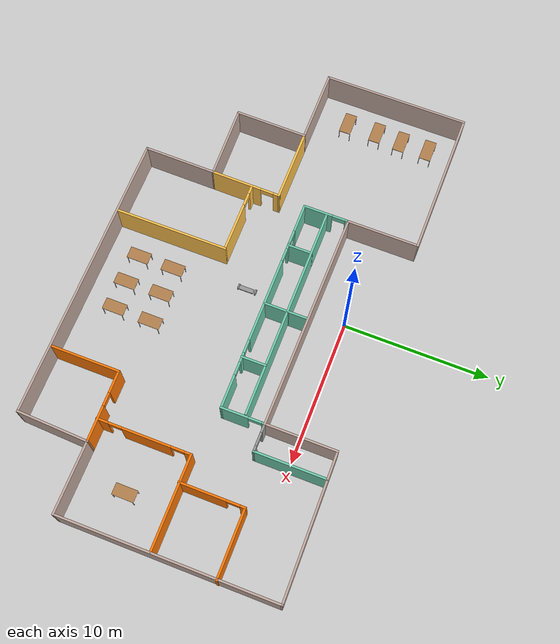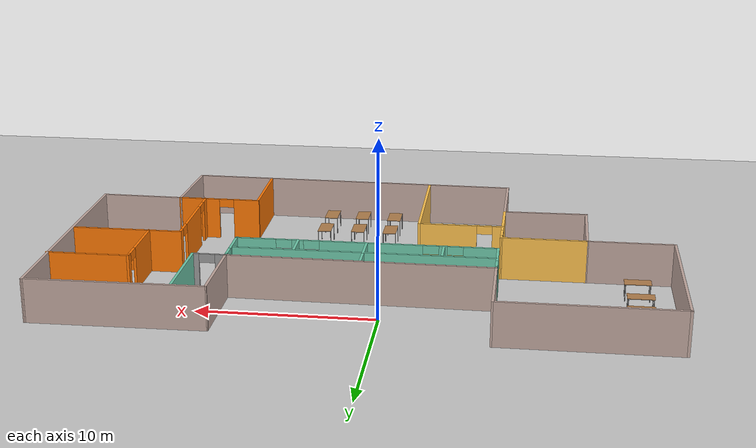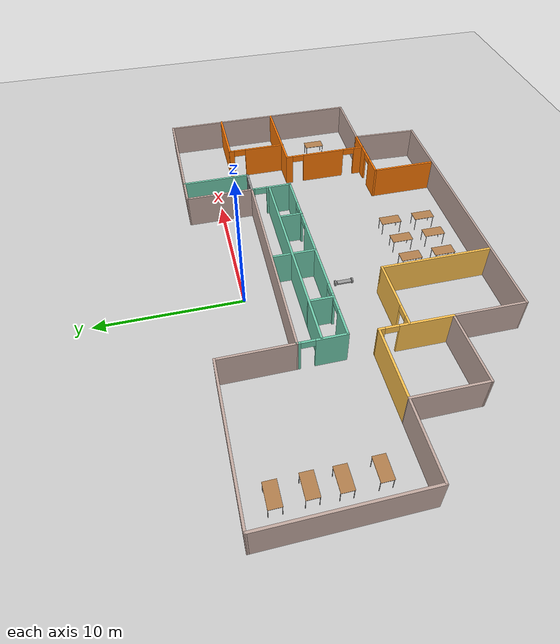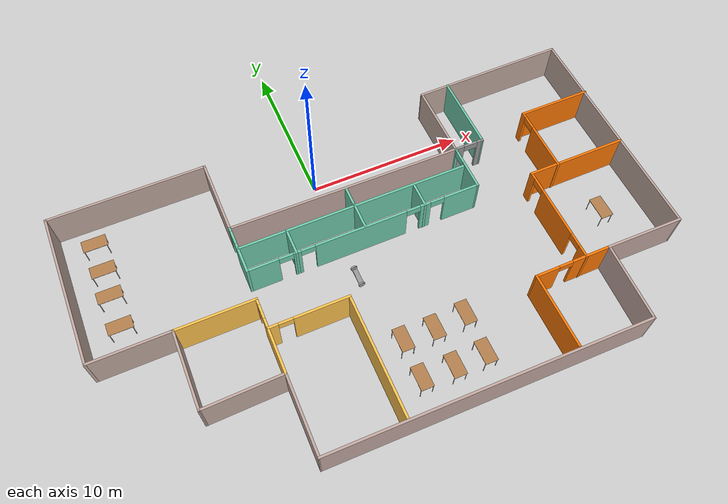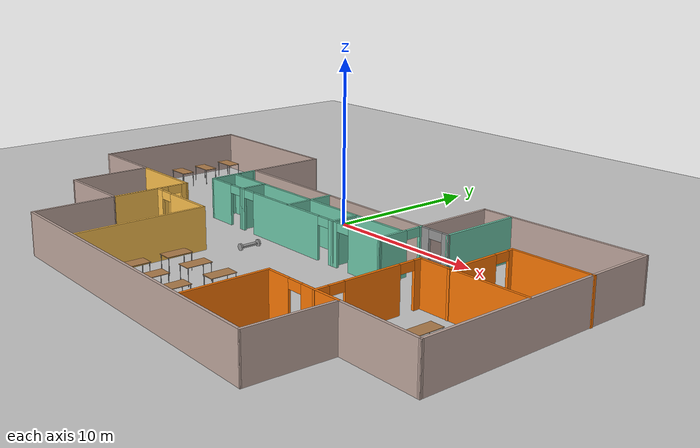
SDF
<sdf version="1.6">
 <world name="default">
  <plugin name="welcome" filename="libwelcome.so"/>
  <light name="sun" type="directional">
   <pose>0 0 10 0 -0 0</pose>
   <diffuse>0.8 0.8 0.8 1</diffuse>
   <specular>0.2 0.2 0.2 1</specular>
   <attenuation>
    <range>1000</range>
    <constant>0.9</constant>
    <linear>0.01</linear>
    <quadratic>0.001</quadratic>
   </attenuation>
   <direction>-0.5 0.1 -0.9</direction>
  </light>
  <model name="ground_plane">
   <static>1</static>
   <link name="link">
    <collision name="collision">
     <geometry><plane><normal>0 0 1</normal><size>100 100</size></plane></geometry>
     <surface>
      <contact><collide_bitmask>65535</collide_bitmask></contact>
      <friction><ode><mu>100</mu><mu2>50</mu2></ode></friction>
     </surface>
    </collision>
    <visual name="visual">
     <cast_shadows>0</cast_shadows>
     <geometry><plane><normal>0 0 1</normal><size>100 100</size></plane></geometry>
     <material>
      <script><uri>file://media/materials/scripts/gazebo.material</uri><name>Gazebo/Grey</name></script>
     </material>
    </visual>
   </link>
  </model>
  <gravity>0 0 -9.8</gravity>
  <magnetic_field>6e-06 2.3e-05 -4.2e-05</magnetic_field>
  <atmosphere type="adiabatic"/>
  <physics name="default_physics" default="0" type="ode">
   <max_step_size>0.001</max_step_size>
   <real_time_factor>1</real_time_factor>
   <real_time_update_rate>1000</real_time_update_rate>
  </physics>
  <scene><ambient>0.4 0.4 0.4 1</ambient><background>0.7 0.7 0.7 1</background><shadows>1</shadows></scene>
  <spherical_coordinates>
   <surface_model>EARTH_WGS84</surface_model>
   <latitude_deg>0</latitude_deg>
   <longitude_deg>0</longitude_deg>
   <elevation>0</elevation>
   <heading_deg>0</heading_deg>
  </spherical_coordinates>
  <model name="Building">
   <pose>1.3137 -7.11076 0 0 -0 0</pose>
   <link name="Wall_0">
    <collision name="Wall_0_Collision">
     <geometry><box><size>10 0.15 2.5</size></box></geometry>
     <pose>0 0 1.25 0 -0 0</pose>
    </collision>
    <visual name="Wall_0_Visual">
     <pose>0 0 1.25 0 -0 0</pose>
     <geometry><box><size>10 0.15 2.5</size></box></geometry>
     <material>
      <script><uri>file://media/materials/scripts/gazebo.material</uri><name>Gazebo/Grey</name></script>
      <ambient>0.760784 0.662745 0.627451 1</ambient>
     </material>
     <meta><layer>0</layer></meta>
    </visual>
    <pose>-12.3733 9.85668 0 0 0 -0.001793</pose>
   </link>
   <link name="Wall_1">
    <collision name="Wall_1_Collision">
     <geometry><box><size>5 0.15 2.5</size></box></geometry>
     <pose>0 0 1.25 0 -0 0</pose>
    </collision>
    <visual name="Wall_1_Visual">
     <pose>0 0 1.25 0 -0 0</pose>
     <geometry><box><size>5 0.15 2.5</size></box></geometry>
     <material>
      <script><uri>file://media/materials/scripts/gazebo.material</uri><name>Gazebo/Grey</name></script>
      <ambient>0.760784 0.662745 0.627451 1</ambient>
     </material>
     <meta><layer>0</layer></meta>
    </visual>
    <pose>-7.44769 7.42291 0 0 0 -1.57056</pose>
   </link>
   <link name="Wall_10">
    <collision name="Wall_10_Collision">
     <geometry><box><size>4.99971 0.15 2.5</size></box></geometry>
     <pose>0 0 1.25 0 -0 0</pose>
    </collision>
    <visual name="Wall_10_Visual">
     <pose>0 0 1.25 0 -0 0</pose>
     <geometry><box><size>4.99971 0.15 2.5</size></box></geometry>
     <material>
      <script><uri>file://media/materials/scripts/gazebo.material</uri><name>Gazebo/Grey</name></script>
      <ambient>0.760784 0.662745 0.627451 1</ambient>
     </material>
     <meta><layer>0</layer></meta>
    </visual>
    <pose>-10.0229 -4.78917 0 0 0 -3.1229</pose>
   </link>
   <link name="Wall_11">
    <collision name="Wall_11_Collision">
     <geometry><box><size>5 0.15 2.5</size></box></geometry>
     <pose>0 0 1.25 0 -0 0</pose>
    </collision>
    <visual name="Wall_11_Visual">
     <pose>0 0 1.25 0 -0 0</pose>
     <geometry><box><size>5 0.15 2.5</size></box></geometry>
     <material>
      <script><uri>file://media/materials/scripts/gazebo.material</uri><name>Gazebo/Grey</name></script>
      <ambient>0.760784 0.662745 0.627451 1</ambient>
     </material>
     <meta><layer>0</layer></meta>
    </visual>
    <pose>-12.4242 -2.40949 0 0 -0 1.56126</pose>
   </link>
   <link name="Wall_12">
    <collision name="Wall_12_Collision">
     <geometry><box><size>5 0.15 2.5</size></box></geometry>
     <pose>0 0 1.25 0 -0 0</pose>
    </collision>
    <visual name="Wall_12_Visual">
     <pose>0 0 1.25 0 -0 0</pose>
     <geometry><box><size>5 0.15 2.5</size></box></geometry>
     <material>
      <script><uri>file://media/materials/scripts/gazebo.material</uri><name>Gazebo/Grey</name></script>
      <ambient>0.760784 0.662745 0.627451 1</ambient>
     </material>
     <meta><layer>0</layer></meta>
    </visual>
    <pose>-14.826 0.015509 0 0 -0 3.14159</pose>
   </link>
   <link name="Wall_13">
    <collision name="Wall_13_Collision">
     <geometry><box><size>10.001 0.15 2.5</size></box></geometry>
     <pose>0 0 1.25 0 -0 0</pose>
    </collision>
    <visual name="Wall_13_Visual">
     <pose>0 0 1.25 0 -0 0</pose>
     <geometry><box><size>10.001 0.15 2.5</size></box></geometry>
     <material>
      <script><uri>file://media/materials/scripts/gazebo.material</uri><name>Gazebo/Grey</name></script>
      <ambient>0.760784 0.662745 0.627451 1</ambient>
     </material>
     <meta><layer>0</layer></meta>
    </visual>
    <pose>-17.2978 4.94051 0 0 -0 1.57089</pose>
   </link>
   <link name="Wall_15">
    <collision name="Wall_15_Collision">
     <geometry><box><size>5 0.15 2.5</size></box></geometry>
     <pose>0 0 1.25 0 -0 0</pose>
    </collision>
    <visual name="Wall_15_Visual">
     <pose>0 0 1.25 0 -0 0</pose>
     <geometry><box><size>5 0.15 2.5</size></box></geometry>
     <material>
      <script><uri>file://media/materials/scripts/gazebo.material</uri><name>Gazebo/Grey</name></script>
      <ambient>1 0.764706 0.305882 1</ambient>
     </material>
     <meta><layer>0</layer></meta>
    </visual>
    <pose>-9.97604 0.015509 0 0 -0 0</pose>
   </link>
   <link name="Wall_16">
    <pose>-7.57474 -2.36417 0 0 0 -1.58075</pose>
    <visual name="Wall_16_Visual_0">
     <pose>-2.22457 0 1.25 0 -0 0</pose>
     <geometry><box><size>0.460463 0.15 2.5</size></box></geometry>
     <material>
      <script><uri>file://media/materials/scripts/gazebo.material</uri><name>Gazebo/Grey</name></script>
      <ambient>1 0.764706 0.305882 1</ambient>
     </material>
     <meta><layer>0</layer></meta>
    </visual>
    <collision name="Wall_16_Collision_0">
     <geometry><box><size>0.460463 0.15 2.5</size></box></geometry>
     <pose>-2.22457 0 1.25 0 -0 0</pose>
    </collision>
    <visual name="Wall_16_Visual_1">
     <pose>0.680232 0 1.25 0 -0 0</pose>
     <geometry><box><size>3.54913 0.15 2.5</size></box></geometry>
     <material>
      <script><uri>file://media/materials/scripts/gazebo.material</uri><name>Gazebo/Grey</name></script>
      <ambient>1 0.764706 0.305882 1</ambient>
     </material>
     <meta><layer>0</layer></meta>
    </visual>
    <collision name="Wall_16_Collision_1">
     <geometry><box><size>3.54913 0.15 2.5</size></box></geometry>
     <pose>0.680232 0 1.25 0 -0 0</pose>
    </collision>
    <visual name="Wall_16_Visual_2">
     <pose>-1.54433 0 2.25 0 -0 0</pose>
     <geometry><box><size>0.9 0.15 0.5</size></box></geometry>
     <material>
      <script><uri>file://media/materials/scripts/gazebo.material</uri><name>Gazebo/Grey</name></script>
      <ambient>1 0.764706 0.305882 1</ambient>
     </material>
     <meta><layer>0</layer></meta>
    </visual>
    <collision name="Wall_16_Collision_2">
     <geometry><box><size>0.9 0.15 0.5</size></box></geometry>
     <pose>-1.54433 0 2.25 0 -0 0</pose>
    </collision>
   </link>
   <link name="Wall_18">
    <pose>-5.11415 -1.91143 0 0 -0 0</pose>
    <visual name="Wall_18_Visual_0">
     <pose>-2.18036 0 1.25 0 -0 0</pose>
     <geometry><box><size>0.639275 0.15 2.5</size></box></geometry>
     <material>
      <script><uri>file://media/materials/scripts/gazebo.material</uri><name>Gazebo/Grey</name></script>
      <ambient>1 0.764706 0.305882 1</ambient>
     </material>
     <meta><layer>0</layer></meta>
    </visual>
    <collision name="Wall_18_Collision_0">
     <geometry><box><size>0.639275 0.15 2.5</size></box></geometry>
     <pose>-2.18036 0 1.25 0 -0 0</pose>
    </collision>
    <visual name="Wall_18_Visual_1">
     <pose>0.769638 0 1.25 0 -0 0</pose>
     <geometry><box><size>3.46073 0.15 2.5</size></box></geometry>
     <material>
      <script><uri>file://media/materials/scripts/gazebo.material</uri><name>Gazebo/Grey</name></script>
      <ambient>1 0.764706 0.305882 1</ambient>
     </material>
     <meta><layer>0</layer></meta>
    </visual>
    <collision name="Wall_18_Collision_1">
     <geometry><box><size>3.46073 0.15 2.5</size></box></geometry>
     <pose>0.769638 0 1.25 0 -0 0</pose>
    </collision>
    <visual name="Wall_18_Visual_2">
     <pose>-1.41073 0 2.25 0 -0 0</pose>
     <geometry><box><size>0.9 0.15 0.5</size></box></geometry>
     <material>
      <script><uri>file://media/materials/scripts/gazebo.material</uri><name>Gazebo/Grey</name></script>
      <ambient>1 0.764706 0.305882 1</ambient>
     </material>
     <meta><layer>0</layer></meta>
    </visual>
    <collision name="Wall_18_Collision_2">
     <geometry><box><size>0.9 0.15 0.5</size></box></geometry>
     <pose>-1.41073 0 2.25 0 -0 0</pose>
    </collision>
   </link>
   <link name="Wall_19">
    <collision name="Wall_19_Collision">
     <geometry><box><size>7.75 0.15 2.5</size></box></geometry>
     <pose>0 0 1.25 0 -0 0</pose>
    </collision>
    <visual name="Wall_19_Visual">
     <pose>0 0 1.25 0 -0 0</pose>
     <geometry><box><size>7.75 0.15 2.5</size></box></geometry>
     <material>
      <script><uri>file://media/materials/scripts/gazebo.material</uri><name>Gazebo/Grey</name></script>
      <ambient>1 0.764706 0.305882 1</ambient>
     </material>
     <meta><layer>0</layer></meta>
    </visual>
    <pose>-2.68915 -5.71143 0 0 0 -1.5708</pose>
   </link>
   <link name="Wall_2">
    <collision name="Wall_2_Collision">
     <geometry><box><size>15 0.15 2.5</size></box></geometry>
     <pose>0 0 1.25 0 -0 0</pose>
    </collision>
    <visual name="Wall_2_Visual">
     <pose>0 0 1.25 0 -0 0</pose>
     <geometry><box><size>15 0.15 2.5</size></box></geometry>
     <material>
      <script><uri>file://media/materials/scripts/gazebo.material</uri><name>Gazebo/Grey</name></script>
      <ambient>0.760784 0.662745 0.627451 1</ambient>
     </material>
     <meta><layer>0</layer></meta>
    </visual>
    <pose>-0.022584 4.91485 0 0 0 -0.011195</pose>
   </link>
   <link name="Wall_21">
    <pose>9.97569 -5.01695 0 0 -0 3.14159</pose>
    <visual name="Wall_21_Visual_0">
     <pose>-1.23973 0 1.25 0 -0 0</pose>
     <geometry><box><size>2.52055 0.15 2.5</size></box></geometry>
     <material>
      <script><uri>file://media/materials/scripts/gazebo.material</uri><name>Gazebo/Grey</name></script>
      <ambient>0.996078 0.47451 0.0196078 1</ambient>
     </material>
     <meta><layer>0</layer></meta>
    </visual>
    <collision name="Wall_21_Collision_0">
     <geometry><box><size>2.52055 0.15 2.5</size></box></geometry>
     <pose>-1.23973 0 1.25 0 -0 0</pose>
    </collision>
    <visual name="Wall_21_Visual_1">
     <pose>1.71027 0 1.25 0 -0 0</pose>
     <geometry><box><size>1.57945 0.15 2.5</size></box></geometry>
     <material>
      <script><uri>file://media/materials/scripts/gazebo.material</uri><name>Gazebo/Grey</name></script>
      <ambient>0.996078 0.47451 0.0196078 1</ambient>
     </material>
     <meta><layer>0</layer></meta>
    </visual>
    <collision name="Wall_21_Collision_1">
     <geometry><box><size>1.57945 0.15 2.5</size></box></geometry>
     <pose>1.71027 0 1.25 0 -0 0</pose>
    </collision>
    <visual name="Wall_21_Visual_2">
     <pose>0.470546 0 2.25 0 -0 0</pose>
     <geometry><box><size>0.9 0.15 0.5</size></box></geometry>
     <material>
      <script><uri>file://media/materials/scripts/gazebo.material</uri><name>Gazebo/Grey</name></script>
      <ambient>0.996078 0.47451 0.0196078 1</ambient>
     </material>
     <meta><layer>0</layer></meta>
    </visual>
    <collision name="Wall_21_Collision_2">
     <geometry><box><size>0.9 0.15 0.5</size></box></geometry>
     <pose>0.470546 0 2.25 0 -0 0</pose>
    </collision>
   </link>
   <link name="Wall_22">
    <collision name="Wall_22_Collision">
     <geometry><box><size>4.75 0.15 2.5</size></box></geometry>
     <pose>0 0 1.25 0 -0 0</pose>
    </collision>
    <visual name="Wall_22_Visual">
     <pose>0 0 1.25 0 -0 0</pose>
     <geometry><box><size>4.75 0.15 2.5</size></box></geometry>
     <material>
      <script><uri>file://media/materials/scripts/gazebo.material</uri><name>Gazebo/Grey</name></script>
      <ambient>0.996078 0.47451 0.0196078 1</ambient>
     </material>
     <meta><layer>0</layer></meta>
    </visual>
    <pose>7.55069 -7.31695 0 0 0 -1.5708</pose>
   </link>
   <link name="Wall_24">
    <pose>-7.44712 3.44797 0 0 0 -1.5708</pose>
    <visual name="Wall_24_Visual_0">
     <pose>-1.47429 0 1.25 0 -0 0</pose>
     <geometry><box><size>0.301423 0.15 2.5</size></box></geometry>
     <material>
      <script><uri>file://media/materials/scripts/gazebo.material</uri><name>Gazebo/Grey</name></script>
      <ambient>0.435294 0.796078 0.67451 1</ambient>
     </material>
     <meta><layer>0</layer></meta>
    </visual>
    <collision name="Wall_24_Collision_0">
     <geometry><box><size>0.301423 0.15 2.5</size></box></geometry>
     <pose>-1.47429 0 1.25 0 -0 0</pose>
    </collision>
    <visual name="Wall_24_Visual_1">
     <pose>0.600711 0 1.25 0 -0 0</pose>
     <geometry><box><size>2.04858 0.15 2.5</size></box></geometry>
     <material>
      <script><uri>file://media/materials/scripts/gazebo.material</uri><name>Gazebo/Grey</name></script>
      <ambient>0.435294 0.796078 0.67451 1</ambient>
     </material>
     <meta><layer>0</layer></meta>
    </visual>
    <collision name="Wall_24_Collision_1">
     <geometry><box><size>2.04858 0.15 2.5</size></box></geometry>
     <pose>0.600711 0 1.25 0 -0 0</pose>
    </collision>
    <visual name="Wall_24_Visual_2">
     <pose>-0.873577 0 2.25 0 -0 0</pose>
     <geometry><box><size>0.9 0.15 0.5</size></box></geometry>
     <material>
      <script><uri>file://media/materials/scripts/gazebo.material</uri><name>Gazebo/Grey</name></script>
      <ambient>0.435294 0.796078 0.67451 1</ambient>
     </material>
     <meta><layer>0</layer></meta>
    </visual>
    <collision name="Wall_24_Collision_2">
     <geometry><box><size>0.9 0.15 0.5</size></box></geometry>
     <pose>-0.873577 0 2.25 0 -0 0</pose>
    </collision>
   </link>
   <link name="Wall_25">
    <pose>-0.022119 1.89797 0 0 -0 0</pose>
    <visual name="Wall_25_Visual_0">
     <pose>-6.49636 0 1.25 0 -0 0</pose>
     <geometry><box><size>2.00728 0.15 2.5</size></box></geometry>
     <material>
      <script><uri>file://media/materials/scripts/gazebo.material</uri><name>Gazebo/Grey</name></script>
      <ambient>0.435294 0.796078 0.67451 1</ambient>
     </material>
     <meta><layer>0</layer></meta>
    </visual>
    <collision name="Wall_25_Collision_0">
     <geometry><box><size>2.00728 0.15 2.5</size></box></geometry>
     <pose>-6.49636 0 1.25 0 -0 0</pose>
    </collision>
    <visual name="Wall_25_Visual_1">
     <pose>-4.35832 0 1.25 0 -0 0</pose>
     <geometry><box><size>0.468788 0.15 2.5</size></box></geometry>
     <material>
      <script><uri>file://media/materials/scripts/gazebo.material</uri><name>Gazebo/Grey</name></script>
      <ambient>0.435294 0.796078 0.67451 1</ambient>
     </material>
     <meta><layer>0</layer></meta>
    </visual>
    <collision name="Wall_25_Collision_1">
     <geometry><box><size>0.468788 0.15 2.5</size></box></geometry>
     <pose>-4.35832 0 1.25 0 -0 0</pose>
    </collision>
    <visual name="Wall_25_Visual_2">
     <pose>-0.282378 0 1.25 0 -0 0</pose>
     <geometry><box><size>5.8831 0.15 2.5</size></box></geometry>
     <material>
      <script><uri>file://media/materials/scripts/gazebo.material</uri><name>Gazebo/Grey</name></script>
      <ambient>0.435294 0.796078 0.67451 1</ambient>
     </material>
     <meta><layer>0</layer></meta>
    </visual>
    <collision name="Wall_25_Collision_2">
     <geometry><box><size>5.8831 0.15 2.5</size></box></geometry>
     <pose>-0.282378 0 1.25 0 -0 0</pose>
    </collision>
    <visual name="Wall_25_Visual_3">
     <pose>3.90003 0 1.25 0 -0 0</pose>
     <geometry><box><size>0.68171 0.15 2.5</size></box></geometry>
     <material>
      <script><uri>file://media/materials/scripts/gazebo.material</uri><name>Gazebo/Grey</name></script>
      <ambient>0.435294 0.796078 0.67451 1</ambient>
     </material>
     <meta><layer>0</layer></meta>
    </visual>
    <collision name="Wall_25_Collision_3">
     <geometry><box><size>0.68171 0.15 2.5</size></box></geometry>
     <pose>3.90003 0 1.25 0 -0 0</pose>
    </collision>
    <visual name="Wall_25_Visual_4">
     <pose>6.32044 0 1.25 0 -0 0</pose>
     <geometry><box><size>2.35912 0.15 2.5</size></box></geometry>
     <material>
      <script><uri>file://media/materials/scripts/gazebo.material</uri><name>Gazebo/Grey</name></script>
      <ambient>0.435294 0.796078 0.67451 1</ambient>
     </material>
     <meta><layer>0</layer></meta>
    </visual>
    <collision name="Wall_25_Collision_4">
     <geometry><box><size>2.35912 0.15 2.5</size></box></geometry>
     <pose>6.32044 0 1.25 0 -0 0</pose>
    </collision>
    <visual name="Wall_25_Visual_5">
     <pose>-5.04272 0 2.25 0 -0 0</pose>
     <geometry><box><size>0.9 0.15 0.5</size></box></geometry>
     <material>
      <script><uri>file://media/materials/scripts/gazebo.material</uri><name>Gazebo/Grey</name></script>
      <ambient>0.435294 0.796078 0.67451 1</ambient>
     </material>
     <meta><layer>0</layer></meta>
    </visual>
    <collision name="Wall_25_Collision_5">
     <geometry><box><size>0.9 0.15 0.5</size></box></geometry>
     <pose>-5.04272 0 2.25 0 -0 0</pose>
    </collision>
    <visual name="Wall_25_Visual_6">
     <pose>-3.67393 0 2.25 0 -0 0</pose>
     <geometry><box><size>0.9 0.15 0.5</size></box></geometry>
     <material>
      <script><uri>file://media/materials/scripts/gazebo.material</uri><name>Gazebo/Grey</name></script>
      <ambient>0.435294 0.796078 0.67451 1</ambient>
     </material>
     <meta><layer>0</layer></meta>
    </visual>
    <collision name="Wall_25_Collision_6">
     <geometry><box><size>0.9 0.15 0.5</size></box></geometry>
     <pose>-3.67393 0 2.25 0 -0 0</pose>
    </collision>
    <visual name="Wall_25_Visual_7">
     <pose>3.10917 0 2.25 0 -0 0</pose>
     <geometry><box><size>0.9 0.15 0.5</size></box></geometry>
     <material>
      <script><uri>file://media/materials/scripts/gazebo.material</uri><name>Gazebo/Grey</name></script>
      <ambient>0.435294 0.796078 0.67451 1</ambient>
     </material>
     <meta><layer>0</layer></meta>
    </visual>
    <collision name="Wall_25_Collision_7">
     <geometry><box><size>0.9 0.15 0.5</size></box></geometry>
     <pose>3.10917 0 2.25 0 -0 0</pose>
    </collision>
    <visual name="Wall_25_Visual_8">
     <pose>4.69088 0 2.25 0 -0 0</pose>
     <geometry><box><size>0.9 0.15 0.5</size></box></geometry>
     <material>
      <script><uri>file://media/materials/scripts/gazebo.material</uri><name>Gazebo/Grey</name></script>
      <ambient>0.435294 0.796078 0.67451 1</ambient>
     </material>
     <meta><layer>0</layer></meta>
    </visual>
    <collision name="Wall_25_Collision_8">
     <geometry><box><size>0.9 0.15 0.5</size></box></geometry>
     <pose>4.69088 0 2.25 0 -0 0</pose>
    </collision>
   </link>
   <link name="Wall_26">
    <pose>7.40242 3.36485 0 0 -0 1.57111</pose>
    <visual name="Wall_26_Visual_0">
     <pose>-0.593608 0 1.25 0 -0 0</pose>
     <geometry><box><size>1.89655 0.15 2.5</size></box></geometry>
     <material>
      <script><uri>file://media/materials/scripts/gazebo.material</uri><name>Gazebo/Grey</name></script>
      <ambient>0.435294 0.796078 0.67451 1</ambient>
     </material>
     <meta><layer>0</layer></meta>
    </visual>
    <collision name="Wall_26_Collision_0">
     <geometry><box><size>1.89655 0.15 2.5</size></box></geometry>
     <pose>-0.593608 0 1.25 0 -0 0</pose>
    </collision>
    <visual name="Wall_26_Visual_1">
     <pose>1.39827 0 1.25 0 -0 0</pose>
     <geometry><box><size>0.287215 0.15 2.5</size></box></geometry>
     <material>
      <script><uri>file://media/materials/scripts/gazebo.material</uri><name>Gazebo/Grey</name></script>
      <ambient>0.435294 0.796078 0.67451 1</ambient>
     </material>
     <meta><layer>0</layer></meta>
    </visual>
    <collision name="Wall_26_Collision_1">
     <geometry><box><size>0.287215 0.15 2.5</size></box></geometry>
     <pose>1.39827 0 1.25 0 -0 0</pose>
    </collision>
    <visual name="Wall_26_Visual_2">
     <pose>0.804666 0 2.25 0 -0 0</pose>
     <geometry><box><size>0.9 0.15 0.5</size></box></geometry>
     <material>
      <script><uri>file://media/materials/scripts/gazebo.material</uri><name>Gazebo/Grey</name></script>
      <ambient>0.435294 0.796078 0.67451 1</ambient>
     </material>
     <meta><layer>0</layer></meta>
    </visual>
    <collision name="Wall_26_Collision_2">
     <geometry><box><size>0.9 0.15 0.5</size></box></geometry>
     <pose>0.804666 0 2.25 0 -0 0</pose>
    </collision>
   </link>
   <link name="Wall_28">
    <collision name="Wall_28_Collision">
     <geometry><box><size>14.75 0.15 2.5</size></box></geometry>
     <pose>0 0 1.25 0 -0 0</pose>
    </collision>
    <visual name="Wall_28_Visual">
     <pose>0 0 1.25 0 -0 0</pose>
     <geometry><box><size>14.75 0.15 2.5</size></box></geometry>
     <material>
      <script><uri>file://media/materials/scripts/gazebo.material</uri><name>Gazebo/Grey</name></script>
      <ambient>0.435294 0.796078 0.67451 1</ambient>
     </material>
     <meta><layer>0</layer></meta>
    </visual>
    <pose>-0.074889 3.49771 0 0 -0 0</pose>
   </link>
   <link name="Wall_3">
    <collision name="Wall_3_Collision">
     <geometry><box><size>4.977 0.15 2.5</size></box></geometry>
     <pose>0 0 1.25 0 -0 0</pose>
    </collision>
    <visual name="Wall_3_Visual">
     <pose>0 0 1.25 0 -0 0</pose>
     <geometry><box><size>4.977 0.15 2.5</size></box></geometry>
     <material>
      <script><uri>file://media/materials/scripts/gazebo.material</uri><name>Gazebo/Grey</name></script>
      <ambient>0.760784 0.662745 0.627451 1</ambient>
     </material>
     <meta><layer>0</layer></meta>
    </visual>
    <pose>7.40161 7.24525 0 0 -0 1.57094</pose>
   </link>
   <link name="Wall_30">
    <collision name="Wall_30_Collision">
     <geometry><box><size>1.5 0.15 2.5</size></box></geometry>
     <pose>0 0 1.25 0 -0 0</pose>
    </collision>
    <visual name="Wall_30_Visual">
     <pose>0 0 1.25 0 -0 0</pose>
     <geometry><box><size>1.5 0.15 2.5</size></box></geometry>
     <material>
      <script><uri>file://media/materials/scripts/gazebo.material</uri><name>Gazebo/Grey</name></script>
      <ambient>0.435294 0.796078 0.67451 1</ambient>
     </material>
     <meta><layer>0</layer></meta>
    </visual>
    <pose>-0.057706 4.22986 0 0 0 -1.5708</pose>
   </link>
   <link name="Wall_32">
    <collision name="Wall_32_Collision">
     <geometry><box><size>1.75 0.15 2.5</size></box></geometry>
     <pose>0 0 1.25 0 -0 0</pose>
    </collision>
    <visual name="Wall_32_Visual">
     <pose>0 0 1.25 0 -0 0</pose>
     <geometry><box><size>1.75 0.15 2.5</size></box></geometry>
     <material>
      <script><uri>file://media/materials/scripts/gazebo.material</uri><name>Gazebo/Grey</name></script>
      <ambient>0.435294 0.796078 0.67451 1</ambient>
     </material>
     <meta><layer>0</layer></meta>
    </visual>
    <pose>-4.41987 2.69771 0 0 0 -1.5708</pose>
   </link>
   <link name="Wall_36">
    <collision name="Wall_36_Collision">
     <geometry><box><size>1.75 0.15 2.5</size></box></geometry>
     <pose>0 0 1.25 0 -0 0</pose>
    </collision>
    <visual name="Wall_36_Visual">
     <pose>0 0 1.25 0 -0 0</pose>
     <geometry><box><size>1.75 0.15 2.5</size></box></geometry>
     <material>
      <script><uri>file://media/materials/scripts/gazebo.material</uri><name>Gazebo/Grey</name></script>
      <ambient>0.435294 0.796078 0.67451 1</ambient>
     </material>
     <meta><layer>0</layer></meta>
    </visual>
    <pose>-0.057706 2.75486 0 0 0 -1.5708</pose>
   </link>
   <link name="Wall_38">
    <collision name="Wall_38_Collision">
     <geometry><box><size>1.75 0.15 2.5</size></box></geometry>
     <pose>0 0 1.25 0 -0 0</pose>
    </collision>
    <visual name="Wall_38_Visual">
     <pose>0 0 1.25 0 -0 0</pose>
     <geometry><box><size>1.75 0.15 2.5</size></box></geometry>
     <material>
      <script><uri>file://media/materials/scripts/gazebo.material</uri><name>Gazebo/Grey</name></script>
      <ambient>0.435294 0.796078 0.67451 1</ambient>
     </material>
     <meta><layer>0</layer></meta>
    </visual>
    <pose>3.84532 2.68439 0 0 0 -1.5708</pose>
   </link>
   <link name="Wall_4">
    <collision name="Wall_4_Collision">
     <geometry><box><size>10 0.15 2.5</size></box></geometry>
     <pose>0 0 1.25 0 -0 0</pose>
    </collision>
    <visual name="Wall_4_Visual">
     <pose>0 0 1.25 0 -0 0</pose>
     <geometry><box><size>10 0.15 2.5</size></box></geometry>
     <material>
      <script><uri>file://media/materials/scripts/gazebo.material</uri><name>Gazebo/Grey</name></script>
      <ambient>0.760784 0.662745 0.627451 1</ambient>
     </material>
     <meta><layer>0</layer></meta>
    </visual>
    <pose>12.3258 9.71227 0 0 -0 0.010864</pose>
   </link>
   <link name="Wall_40">
    <collision name="Wall_40_Collision">
     <geometry><box><size>5 0.15 2.5</size></box></geometry>
     <pose>0 0 1.25 0 -0 0</pose>
    </collision>
    <visual name="Wall_40_Visual">
     <pose>0 0 1.25 0 -0 0</pose>
     <geometry><box><size>5 0.15 2.5</size></box></geometry>
     <material>
      <script><uri>file://media/materials/scripts/gazebo.material</uri><name>Gazebo/Grey</name></script>
      <ambient>0.435294 0.796078 0.67451 1</ambient>
     </material>
     <meta><layer>0</layer></meta>
    </visual>
    <pose>9.26532 7.23939 0 0 0 -1.5708</pose>
   </link>
   <link name="Wall_41">
    <pose>8.33363 4.82306 0 0 -0 3.13228</pose>
    <visual name="Wall_41_Visual_0">
     <pose>-0.781737 0 1.25 0 -0 0</pose>
     <geometry><box><size>0.449972 0.15 2.5</size></box></geometry>
     <material>
      <script><uri>file://media/materials/scripts/gazebo.material</uri><name>Gazebo/Grey</name></script>
      <ambient>1 1 1 1</ambient>
     </material>
     <meta><layer>0</layer></meta>
    </visual>
    <collision name="Wall_41_Collision_0">
     <geometry><box><size>0.449972 0.15 2.5</size></box></geometry>
     <pose>-0.781737 0 1.25 0 -0 0</pose>
    </collision>
    <visual name="Wall_41_Visual_1">
     <pose>0.674986 0 1.25 0 -0 0</pose>
     <geometry><box><size>0.663474 0.15 2.5</size></box></geometry>
     <material>
      <script><uri>file://media/materials/scripts/gazebo.material</uri><name>Gazebo/Grey</name></script>
      <ambient>1 1 1 1</ambient>
     </material>
     <meta><layer>0</layer></meta>
    </visual>
    <collision name="Wall_41_Collision_1">
     <geometry><box><size>0.663474 0.15 2.5</size></box></geometry>
     <pose>0.674986 0 1.25 0 -0 0</pose>
    </collision>
    <visual name="Wall_41_Visual_2">
     <pose>-0.106751 0 2.25 0 -0 0</pose>
     <geometry><box><size>0.9 0.15 0.5</size></box></geometry>
     <material>
      <script><uri>file://media/materials/scripts/gazebo.material</uri><name>Gazebo/Grey</name></script>
      <ambient>1 1 1 1</ambient>
     </material>
     <meta><layer>0</layer></meta>
    </visual>
    <collision name="Wall_41_Collision_2">
     <geometry><box><size>0.9 0.15 0.5</size></box></geometry>
     <pose>-0.106751 0 2.25 0 -0 0</pose>
    </collision>
   </link>
   <link name="Wall_43">
    <pose>10.8479 -1.87139 0 0 -0 1.5708</pose>
    <visual name="Wall_43_Visual_0">
     <pose>-2.82948 0 1.25 0 -0 0</pose>
     <geometry><box><size>0.841047 0.15 2.5</size></box></geometry>
     <material>
      <script><uri>file://media/materials/scripts/gazebo.material</uri><name>Gazebo/Grey</name></script>
      <ambient>0.996078 0.47451 0.0196078 1</ambient>
     </material>
     <meta><layer>0</layer></meta>
    </visual>
    <collision name="Wall_43_Collision_0">
     <geometry><box><size>0.841047 0.15 2.5</size></box></geometry>
     <pose>-2.82948 0 1.25 0 -0 0</pose>
    </collision>
    <visual name="Wall_43_Visual_1">
     <pose>0.155063 0 1.25 0 -0 0</pose>
     <geometry><box><size>3.32803 0.15 2.5</size></box></geometry>
     <material>
      <script><uri>file://media/materials/scripts/gazebo.material</uri><name>Gazebo/Grey</name></script>
      <ambient>0.996078 0.47451 0.0196078 1</ambient>
     </material>
     <meta><layer>0</layer></meta>
    </visual>
    <collision name="Wall_43_Collision_1">
     <geometry><box><size>3.32803 0.15 2.5</size></box></geometry>
     <pose>0.155063 0 1.25 0 -0 0</pose>
    </collision>
    <visual name="Wall_43_Visual_2">
     <pose>2.98454 0 1.25 0 -0 0</pose>
     <geometry><box><size>0.53092 0.15 2.5</size></box></geometry>
     <material>
      <script><uri>file://media/materials/scripts/gazebo.material</uri><name>Gazebo/Grey</name></script>
      <ambient>0.996078 0.47451 0.0196078 1</ambient>
     </material>
     <meta><layer>0</layer></meta>
    </visual>
    <collision name="Wall_43_Collision_2">
     <geometry><box><size>0.53092 0.15 2.5</size></box></geometry>
     <pose>2.98454 0 1.25 0 -0 0</pose>
    </collision>
    <visual name="Wall_43_Visual_3">
     <pose>-1.95895 0 2.25 0 -0 0</pose>
     <geometry><box><size>0.9 0.15 0.5</size></box></geometry>
     <material>
      <script><uri>file://media/materials/scripts/gazebo.material</uri><name>Gazebo/Grey</name></script>
      <ambient>0.996078 0.47451 0.0196078 1</ambient>
     </material>
     <meta><layer>0</layer></meta>
    </visual>
    <collision name="Wall_43_Collision_3">
     <geometry><box><size>0.9 0.15 0.5</size></box></geometry>
     <pose>-1.95895 0 2.25 0 -0 0</pose>
    </collision>
    <visual name="Wall_43_Visual_4">
     <pose>2.26908 0 2.25 0 -0 0</pose>
     <geometry><box><size>0.9 0.15 0.5</size></box></geometry>
     <material>
      <script><uri>file://media/materials/scripts/gazebo.material</uri><name>Gazebo/Grey</name></script>
      <ambient>0.996078 0.47451 0.0196078 1</ambient>
     </material>
     <meta><layer>0</layer></meta>
    </visual>
    <collision name="Wall_43_Collision_4">
     <geometry><box><size>0.9 0.15 0.5</size></box></geometry>
     <pose>2.26908 0 2.25 0 -0 0</pose>
    </collision>
   </link>
   <link name="Wall_44">
    <collision name="Wall_44_Collision">
     <geometry><box><size>6.5 0.15 2.5</size></box></geometry>
     <pose>0 0 1.25 0 -0 0</pose>
    </collision>
    <visual name="Wall_44_Visual">
     <pose>0 0 1.25 0 -0 0</pose>
     <geometry><box><size>6.5 0.15 2.5</size></box></geometry>
     <material>
      <script><uri>file://media/materials/scripts/gazebo.material</uri><name>Gazebo/Grey</name></script>
      <ambient>0.996078 0.47451 0.0196078 1</ambient>
     </material>
     <meta><layer>0</layer></meta>
    </visual>
    <pose>14.0229 1.30361 0 0 -0 0</pose>
   </link>
   <link name="Wall_46">
    <pose>12.6984 3.44428 0 0 -0 1.5708</pose>
    <visual name="Wall_46_Visual_0">
     <pose>-0.652813 0 1.25 0 -0 0</pose>
     <geometry><box><size>3.19437 0.15 2.5</size></box></geometry>
     <material>
      <script><uri>file://media/materials/scripts/gazebo.material</uri><name>Gazebo/Grey</name></script>
      <ambient>0.996078 0.47451 0.0196078 1</ambient>
     </material>
     <meta><layer>0</layer></meta>
    </visual>
    <collision name="Wall_46_Collision_0">
     <geometry><box><size>3.19437 0.15 2.5</size></box></geometry>
     <pose>-0.652813 0 1.25 0 -0 0</pose>
    </collision>
    <visual name="Wall_46_Visual_1">
     <pose>2.04719 0 1.25 0 -0 0</pose>
     <geometry><box><size>0.405627 0.15 2.5</size></box></geometry>
     <material>
      <script><uri>file://media/materials/scripts/gazebo.material</uri><name>Gazebo/Grey</name></script>
      <ambient>0.996078 0.47451 0.0196078 1</ambient>
     </material>
     <meta><layer>0</layer></meta>
    </visual>
    <collision name="Wall_46_Collision_1">
     <geometry><box><size>0.405627 0.15 2.5</size></box></geometry>
     <pose>2.04719 0 1.25 0 -0 0</pose>
    </collision>
    <visual name="Wall_46_Visual_2">
     <pose>1.39437 0 2.25 0 -0 0</pose>
     <geometry><box><size>0.9 0.15 0.5</size></box></geometry>
     <material>
      <script><uri>file://media/materials/scripts/gazebo.material</uri><name>Gazebo/Grey</name></script>
      <ambient>0.996078 0.47451 0.0196078 1</ambient>
     </material>
     <meta><layer>0</layer></meta>
    </visual>
    <collision name="Wall_46_Collision_2">
     <geometry><box><size>0.9 0.15 0.5</size></box></geometry>
     <pose>1.39437 0 2.25 0 -0 0</pose>
    </collision>
   </link>
   <link name="Wall_47">
    <collision name="Wall_47_Collision">
     <geometry><box><size>4.75 0.15 2.5</size></box></geometry>
     <pose>0 0 1.25 0 -0 0</pose>
    </collision>
    <visual name="Wall_47_Visual">
     <pose>0 0 1.25 0 -0 0</pose>
     <geometry><box><size>4.75 0.15 2.5</size></box></geometry>
     <material>
      <script><uri>file://media/materials/scripts/gazebo.material</uri><name>Gazebo/Grey</name></script>
      <ambient>0.996078 0.47451 0.0196078 1</ambient>
     </material>
     <meta><layer>0</layer></meta>
    </visual>
    <pose>14.9984 5.61928 0 0 -0 0</pose>
   </link>
   <link name="Wall_5">
    <collision name="Wall_5_Collision">
     <geometry><box><size>15 0.15 2.5</size></box></geometry>
     <pose>0 0 1.25 0 -0 0</pose>
    </collision>
    <visual name="Wall_5_Visual">
     <pose>0 0 1.25 0 -0 0</pose>
     <geometry><box><size>15 0.15 2.5</size></box></geometry>
     <material>
      <script><uri>file://media/materials/scripts/gazebo.material</uri><name>Gazebo/Grey</name></script>
      <ambient>0.760784 0.662745 0.627451 1</ambient>
     </material>
     <meta><layer>0</layer></meta>
    </visual>
    <pose>17.2503 2.34085 0 0 0 -1.5708</pose>
   </link>
   <link name="Wall_6">
    <collision name="Wall_6_Collision">
     <geometry><box><size>5 0.15 2.5</size></box></geometry>
     <pose>0 0 1.25 0 -0 0</pose>
    </collision>
    <visual name="Wall_6_Visual">
     <pose>0 0 1.25 0 -0 0</pose>
     <geometry><box><size>5 0.15 2.5</size></box></geometry>
     <material>
      <script><uri>file://media/materials/scripts/gazebo.material</uri><name>Gazebo/Grey</name></script>
      <ambient>0.760784 0.662745 0.627451 1</ambient>
     </material>
     <meta><layer>0</layer></meta>
    </visual>
    <pose>14.8255 -5.05051 0 0 -0 3.12775</pose>
   </link>
   <link name="Wall_7">
    <collision name="Wall_7_Collision">
     <geometry><box><size>5 0.15 2.5</size></box></geometry>
     <pose>0 0 1.25 0 -0 0</pose>
    </collision>
    <visual name="Wall_7_Visual">
     <pose>0 0 1.25 0 -0 0</pose>
     <geometry><box><size>5 0.15 2.5</size></box></geometry>
     <material>
      <script><uri>file://media/materials/scripts/gazebo.material</uri><name>Gazebo/Grey</name></script>
      <ambient>0.760784 0.662745 0.627451 1</ambient>
     </material>
     <meta><layer>0</layer></meta>
    </visual>
    <pose>12.3037 -7.44001 0 0 0 -1.61079</pose>
   </link>
   <link name="Wall_8">
    <collision name="Wall_8_Collision">
     <geometry><box><size>20 0.15 2.5</size></box></geometry>
     <pose>0 0 1.25 0 -0 0</pose>
    </collision>
    <visual name="Wall_8_Visual">
     <pose>0 0 1.25 0 -0 0</pose>
     <geometry><box><size>20 0.15 2.5</size></box></geometry>
     <material>
      <script><uri>file://media/materials/scripts/gazebo.material</uri><name>Gazebo/Grey</name></script>
      <ambient>0.760784 0.662745 0.627451 1</ambient>
     </material>
     <meta><layer>0</layer></meta>
    </visual>
    <pose>2.2827 -9.72813 0 0 -0 3.128</pose>
   </link>
   <link name="Wall_9">
    <collision name="Wall_9_Collision">
     <geometry><box><size>4.93835 0.15 2.5</size></box></geometry>
     <pose>0 0 1.25 0 -0 0</pose>
    </collision>
    <visual name="Wall_9_Visual">
     <pose>0 0 1.25 0 -0 0</pose>
     <geometry><box><size>4.93835 0.15 2.5</size></box></geometry>
     <material>
      <script><uri>file://media/materials/scripts/gazebo.material</uri><name>Gazebo/Grey</name></script>
      <ambient>0.760784 0.662745 0.627451 1</ambient>
     </material>
     <meta><layer>0</layer></meta>
    </visual>
    <pose>-7.61991 -7.19911 0 0 -0 1.56183</pose>
   </link>
   <static>1</static>
  </model>
  <model name="table">
   <static>1</static>
   <link name="link">
    <collision name="surface">
     <pose>0 0 1 0 -0 0</pose>
     <geometry><box><size>1.5 0.8 0.03</size></box></geometry>
     <surface><friction><ode><mu>0.6</mu><mu2>0.6</mu2></ode></friction></surface>
    </collision>
    <visual name="visual1">
     <pose>0 0 1 0 -0 0</pose>
     <geometry><box><size>1.5 0.8 0.03</size></box></geometry>
     <material>
      <script><uri>file://media/materials/scripts/gazebo.material</uri><name>Gazebo/Wood</name></script>
     </material>
    </visual>
    <collision name="front_left_leg">
     <pose>0.68 0.38 0.5 0 -0 0</pose>
     <geometry><cylinder><radius>0.02</radius><length>1</length></cylinder></geometry>
    </collision>
    <visual name="front_left_leg">
     <pose>0.68 0.38 0.5 0 -0 0</pose>
     <geometry><cylinder><radius>0.02</radius><length>1</length></cylinder></geometry>
     <material>
      <script><uri>file://media/materials/scripts/gazebo.material</uri><name>Gazebo/Grey</name></script>
     </material>
    </visual>
    <collision name="front_right_leg">
     <pose>0.68 -0.38 0.5 0 -0 0</pose>
     <geometry><cylinder><radius>0.02</radius><length>1</length></cylinder></geometry>
    </collision>
    <visual name="front_right_leg">
     <pose>0.68 -0.38 0.5 0 -0 0</pose>
     <geometry><cylinder><radius>0.02</radius><length>1</length></cylinder></geometry>
     <material>
      <script><uri>file://media/materials/scripts/gazebo.material</uri><name>Gazebo/Grey</name></script>
     </material>
    </visual>
    <collision name="back_right_leg">
     <pose>-0.68 -0.38 0.5 0 -0 0</pose>
     <geometry><cylinder><radius>0.02</radius><length>1</length></cylinder></geometry>
    </collision>
    <visual name="back_right_leg">
     <pose>-0.68 -0.38 0.5 0 -0 0</pose>
     <geometry><cylinder><radius>0.02</radius><length>1</length></cylinder></geometry>
     <material>
      <script><uri>file://media/materials/scripts/gazebo.material</uri><name>Gazebo/Grey</name></script>
     </material>
    </visual>
    <collision name="back_left_leg">
     <pose>-0.68 0.38 0.5 0 -0 0</pose>
     <geometry><cylinder><radius>0.02</radius><length>1</length></cylinder></geometry>
    </collision>
    <visual name="back_left_leg">
     <pose>-0.68 0.38 0.5 0 -0 0</pose>
     <geometry><cylinder><radius>0.02</radius><length>1</length></cylinder></geometry>
     <material>
      <script><uri>file://media/materials/scripts/gazebo.material</uri><name>Gazebo/Grey</name></script>
     </material>
    </visual>
   </link>
   <pose>-13.8763 1.06546 0 0 -0 0</pose>
  </model>
  <model name="table_clone">
   <static>1</static>
   <link name="link">
    <collision name="surface">
     <pose>0 0 1 0 -0 0</pose>
     <geometry><box><size>1.5 0.8 0.03</size></box></geometry>
     <surface><friction><ode><mu>0.6</mu><mu2>0.6</mu2></ode></friction></surface>
    </collision>
    <visual name="visual1">
     <pose>0 0 1 0 -0 0</pose>
     <geometry><box><size>1.5 0.8 0.03</size></box></geometry>
     <material>
      <script><uri>file://media/materials/scripts/gazebo.material</uri><name>Gazebo/Wood</name></script>
     </material>
    </visual>
    <collision name="front_left_leg">
     <pose>0.68 0.38 0.5 0 -0 0</pose>
     <geometry><cylinder><radius>0.02</radius><length>1</length></cylinder></geometry>
    </collision>
    <visual name="front_left_leg">
     <pose>0.68 0.38 0.5 0 -0 0</pose>
     <geometry><cylinder><radius>0.02</radius><length>1</length></cylinder></geometry>
     <material>
      <script><uri>file://media/materials/scripts/gazebo.material</uri><name>Gazebo/Grey</name></script>
     </material>
    </visual>
    <collision name="front_right_leg">
     <pose>0.68 -0.38 0.5 0 -0 0</pose>
     <geometry><cylinder><radius>0.02</radius><length>1</length></cylinder></geometry>
    </collision>
    <visual name="front_right_leg">
     <pose>0.68 -0.38 0.5 0 -0 0</pose>
     <geometry><cylinder><radius>0.02</radius><length>1</length></cylinder></geometry>
     <material>
      <script><uri>file://media/materials/scripts/gazebo.material</uri><name>Gazebo/Grey</name></script>
     </material>
    </visual>
    <collision name="back_right_leg">
     <pose>-0.68 -0.38 0.5 0 -0 0</pose>
     <geometry><cylinder><radius>0.02</radius><length>1</length></cylinder></geometry>
    </collision>
    <visual name="back_right_leg">
     <pose>-0.68 -0.38 0.5 0 -0 0</pose>
     <geometry><cylinder><radius>0.02</radius><length>1</length></cylinder></geometry>
     <material>
      <script><uri>file://media/materials/scripts/gazebo.material</uri><name>Gazebo/Grey</name></script>
     </material>
    </visual>
    <collision name="back_left_leg">
     <pose>-0.68 0.38 0.5 0 -0 0</pose>
     <geometry><cylinder><radius>0.02</radius><length>1</length></cylinder></geometry>
    </collision>
    <visual name="back_left_leg">
     <pose>-0.68 0.38 0.5 0 -0 0</pose>
     <geometry><cylinder><radius>0.02</radius><length>1</length></cylinder></geometry>
     <material>
      <script><uri>file://media/materials/scripts/gazebo.material</uri><name>Gazebo/Grey</name></script>
     </material>
    </visual>
   </link>
   <pose>-13.8476 -0.879372 0 0 -0 0</pose>
  </model>
  <model name="table_clone_0">
   <static>1</static>
   <link name="link">
    <collision name="surface">
     <pose>0 0 1 0 -0 0</pose>
     <geometry><box><size>1.5 0.8 0.03</size></box></geometry>
     <surface><friction><ode><mu>0.6</mu><mu2>0.6</mu2></ode></friction></surface>
    </collision>
    <visual name="visual1">
     <pose>0 0 1 0 -0 0</pose>
     <geometry><box><size>1.5 0.8 0.03</size></box></geometry>
     <material>
      <script><uri>file://media/materials/scripts/gazebo.material</uri><name>Gazebo/Wood</name></script>
     </material>
    </visual>
    <collision name="front_left_leg">
     <pose>0.68 0.38 0.5 0 -0 0</pose>
     <geometry><cylinder><radius>0.02</radius><length>1</length></cylinder></geometry>
    </collision>
    <visual name="front_left_leg">
     <pose>0.68 0.38 0.5 0 -0 0</pose>
     <geometry><cylinder><radius>0.02</radius><length>1</length></cylinder></geometry>
     <material>
      <script><uri>file://media/materials/scripts/gazebo.material</uri><name>Gazebo/Grey</name></script>
     </material>
    </visual>
    <collision name="front_right_leg">
     <pose>0.68 -0.38 0.5 0 -0 0</pose>
     <geometry><cylinder><radius>0.02</radius><length>1</length></cylinder></geometry>
    </collision>
    <visual name="front_right_leg">
     <pose>0.68 -0.38 0.5 0 -0 0</pose>
     <geometry><cylinder><radius>0.02</radius><length>1</length></cylinder></geometry>
     <material>
      <script><uri>file://media/materials/scripts/gazebo.material</uri><name>Gazebo/Grey</name></script>
     </material>
    </visual>
    <collision name="back_right_leg">
     <pose>-0.68 -0.38 0.5 0 -0 0</pose>
     <geometry><cylinder><radius>0.02</radius><length>1</length></cylinder></geometry>
    </collision>
    <visual name="back_right_leg">
     <pose>-0.68 -0.38 0.5 0 -0 0</pose>
     <geometry><cylinder><radius>0.02</radius><length>1</length></cylinder></geometry>
     <material>
      <script><uri>file://media/materials/scripts/gazebo.material</uri><name>Gazebo/Grey</name></script>
     </material>
    </visual>
    <collision name="back_left_leg">
     <pose>-0.68 0.38 0.5 0 -0 0</pose>
     <geometry><cylinder><radius>0.02</radius><length>1</length></cylinder></geometry>
    </collision>
    <visual name="back_left_leg">
     <pose>-0.68 0.38 0.5 0 -0 0</pose>
     <geometry><cylinder><radius>0.02</radius><length>1</length></cylinder></geometry>
     <material>
      <script><uri>file://media/materials/scripts/gazebo.material</uri><name>Gazebo/Grey</name></script>
     </material>
    </visual>
   </link>
   <pose>-13.9125 -2.67326 0 0 -0 0</pose>
  </model>
  <model name="table_clone_1_clone">
   <static>1</static>
   <link name="link">
    <collision name="surface">
     <pose>0 0 1 0 -0 0</pose>
     <geometry><box><size>1.5 0.8 0.03</size></box></geometry>
     <surface><friction><ode><mu>0.6</mu><mu2>0.6</mu2></ode></friction></surface>
    </collision>
    <visual name="visual1">
     <pose>0 0 1 0 -0 0</pose>
     <geometry><box><size>1.5 0.8 0.03</size></box></geometry>
     <material>
      <script><uri>file://media/materials/scripts/gazebo.material</uri><name>Gazebo/Wood</name></script>
     </material>
    </visual>
    <collision name="front_left_leg">
     <pose>0.68 0.38 0.5 0 -0 0</pose>
     <geometry><cylinder><radius>0.02</radius><length>1</length></cylinder></geometry>
    </collision>
    <visual name="front_left_leg">
     <pose>0.68 0.38 0.5 0 -0 0</pose>
     <geometry><cylinder><radius>0.02</radius><length>1</length></cylinder></geometry>
     <material>
      <script><uri>file://media/materials/scripts/gazebo.material</uri><name>Gazebo/Grey</name></script>
     </material>
    </visual>
    <collision name="front_right_leg">
     <pose>0.68 -0.38 0.5 0 -0 0</pose>
     <geometry><cylinder><radius>0.02</radius><length>1</length></cylinder></geometry>
    </collision>
    <visual name="front_right_leg">
     <pose>0.68 -0.38 0.5 0 -0 0</pose>
     <geometry><cylinder><radius>0.02</radius><length>1</length></cylinder></geometry>
     <material>
      <script><uri>file://media/materials/scripts/gazebo.material</uri><name>Gazebo/Grey</name></script>
     </material>
    </visual>
    <collision name="back_right_leg">
     <pose>-0.68 -0.38 0.5 0 -0 0</pose>
     <geometry><cylinder><radius>0.02</radius><length>1</length></cylinder></geometry>
    </collision>
    <visual name="back_right_leg">
     <pose>-0.68 -0.38 0.5 0 -0 0</pose>
     <geometry><cylinder><radius>0.02</radius><length>1</length></cylinder></geometry>
     <material>
      <script><uri>file://media/materials/scripts/gazebo.material</uri><name>Gazebo/Grey</name></script>
     </material>
    </visual>
    <collision name="back_left_leg">
     <pose>-0.68 0.38 0.5 0 -0 0</pose>
     <geometry><cylinder><radius>0.02</radius><length>1</length></cylinder></geometry>
    </collision>
    <visual name="back_left_leg">
     <pose>-0.68 0.38 0.5 0 -0 0</pose>
     <geometry><cylinder><radius>0.02</radius><length>1</length></cylinder></geometry>
     <material>
      <script><uri>file://media/materials/scripts/gazebo.material</uri><name>Gazebo/Grey</name></script>
     </material>
    </visual>
   </link>
   <pose>0.596665 -14.4732 -0.006617 0.010182 0.002048 1.56787</pose>
  </model>
  <model name="table_clone_1_clone_0">
   <static>1</static>
   <link name="link">
    <collision name="surface">
     <pose>0 0 1 0 -0 0</pose>
     <geometry><box><size>1.5 0.8 0.03</size></box></geometry>
     <surface><friction><ode><mu>0.6</mu><mu2>0.6</mu2></ode></friction></surface>
    </collision>
    <visual name="visual1">
     <pose>0 0 1 0 -0 0</pose>
     <geometry><box><size>1.5 0.8 0.03</size></box></geometry>
     <material>
      <script><uri>file://media/materials/scripts/gazebo.material</uri><name>Gazebo/Wood</name></script>
     </material>
    </visual>
    <collision name="front_left_leg">
     <pose>0.68 0.38 0.5 0 -0 0</pose>
     <geometry><cylinder><radius>0.02</radius><length>1</length></cylinder></geometry>
    </collision>
    <visual name="front_left_leg">
     <pose>0.68 0.38 0.5 0 -0 0</pose>
     <geometry><cylinder><radius>0.02</radius><length>1</length></cylinder></geometry>
     <material>
      <script><uri>file://media/materials/scripts/gazebo.material</uri><name>Gazebo/Grey</name></script>
     </material>
    </visual>
    <collision name="front_right_leg">
     <pose>0.68 -0.38 0.5 0 -0 0</pose>
     <geometry><cylinder><radius>0.02</radius><length>1</length></cylinder></geometry>
    </collision>
    <visual name="front_right_leg">
     <pose>0.68 -0.38 0.5 0 -0 0</pose>
     <geometry><cylinder><radius>0.02</radius><length>1</length></cylinder></geometry>
     <material>
      <script><uri>file://media/materials/scripts/gazebo.material</uri><name>Gazebo/Grey</name></script>
     </material>
    </visual>
    <collision name="back_right_leg">
     <pose>-0.68 -0.38 0.5 0 -0 0</pose>
     <geometry><cylinder><radius>0.02</radius><length>1</length></cylinder></geometry>
    </collision>
    <visual name="back_right_leg">
     <pose>-0.68 -0.38 0.5 0 -0 0</pose>
     <geometry><cylinder><radius>0.02</radius><length>1</length></cylinder></geometry>
     <material>
      <script><uri>file://media/materials/scripts/gazebo.material</uri><name>Gazebo/Grey</name></script>
     </material>
    </visual>
    <collision name="back_left_leg">
     <pose>-0.68 0.38 0.5 0 -0 0</pose>
     <geometry><cylinder><radius>0.02</radius><length>1</length></cylinder></geometry>
    </collision>
    <visual name="back_left_leg">
     <pose>-0.68 0.38 0.5 0 -0 0</pose>
     <geometry><cylinder><radius>0.02</radius><length>1</length></cylinder></geometry>
     <material>
      <script><uri>file://media/materials/scripts/gazebo.material</uri><name>Gazebo/Grey</name></script>
     </material>
    </visual>
   </link>
   <pose>0.609249 -12.0113 -0.006617 0.010182 0.002048 1.56787</pose>
  </model>
  <model name="table_clone_1_clone_1">
   <static>1</static>
   <link name="link">
    <collision name="surface">
     <pose>0 0 1 0 -0 0</pose>
     <geometry><box><size>1.5 0.8 0.03</size></box></geometry>
     <surface><friction><ode><mu>0.6</mu><mu2>0.6</mu2></ode></friction></surface>
    </collision>
    <visual name="visual1">
     <pose>0 0 1 0 -0 0</pose>
     <geometry><box><size>1.5 0.8 0.03</size></box></geometry>
     <material>
      <script><uri>file://media/materials/scripts/gazebo.material</uri><name>Gazebo/Wood</name></script>
     </material>
    </visual>
    <collision name="front_left_leg">
     <pose>0.68 0.38 0.5 0 -0 0</pose>
     <geometry><cylinder><radius>0.02</radius><length>1</length></cylinder></geometry>
    </collision>
    <visual name="front_left_leg">
     <pose>0.68 0.38 0.5 0 -0 0</pose>
     <geometry><cylinder><radius>0.02</radius><length>1</length></cylinder></geometry>
     <material>
      <script><uri>file://media/materials/scripts/gazebo.material</uri><name>Gazebo/Grey</name></script>
     </material>
    </visual>
    <collision name="front_right_leg">
     <pose>0.68 -0.38 0.5 0 -0 0</pose>
     <geometry><cylinder><radius>0.02</radius><length>1</length></cylinder></geometry>
    </collision>
    <visual name="front_right_leg">
     <pose>0.68 -0.38 0.5 0 -0 0</pose>
     <geometry><cylinder><radius>0.02</radius><length>1</length></cylinder></geometry>
     <material>
      <script><uri>file://media/materials/scripts/gazebo.material</uri><name>Gazebo/Grey</name></script>
     </material>
    </visual>
    <collision name="back_right_leg">
     <pose>-0.68 -0.38 0.5 0 -0 0</pose>
     <geometry><cylinder><radius>0.02</radius><length>1</length></cylinder></geometry>
    </collision>
    <visual name="back_right_leg">
     <pose>-0.68 -0.38 0.5 0 -0 0</pose>
     <geometry><cylinder><radius>0.02</radius><length>1</length></cylinder></geometry>
     <material>
      <script><uri>file://media/materials/scripts/gazebo.material</uri><name>Gazebo/Grey</name></script>
     </material>
    </visual>
    <collision name="back_left_leg">
     <pose>-0.68 0.38 0.5 0 -0 0</pose>
     <geometry><cylinder><radius>0.02</radius><length>1</length></cylinder></geometry>
    </collision>
    <visual name="back_left_leg">
     <pose>-0.68 0.38 0.5 0 -0 0</pose>
     <geometry><cylinder><radius>0.02</radius><length>1</length></cylinder></geometry>
     <material>
      <script><uri>file://media/materials/scripts/gazebo.material</uri><name>Gazebo/Grey</name></script>
     </material>
    </visual>
   </link>
   <pose>2.555 -12.0632 -0.006617 0.010182 0.002048 1.56787</pose>
  </model>
  <model name="table_clone_1_clone_2">
   <static>1</static>
   <link name="link">
    <collision name="surface">
     <pose>0 0 1 0 -0 0</pose>
     <geometry><box><size>1.5 0.8 0.03</size></box></geometry>
     <surface><friction><ode><mu>0.6</mu><mu2>0.6</mu2></ode></friction></surface>
    </collision>
    <visual name="visual1">
     <pose>0 0 1 0 -0 0</pose>
     <geometry><box><size>1.5 0.8 0.03</size></box></geometry>
     <material>
      <script><uri>file://media/materials/scripts/gazebo.material</uri><name>Gazebo/Wood</name></script>
     </material>
    </visual>
    <collision name="front_left_leg">
     <pose>0.68 0.38 0.5 0 -0 0</pose>
     <geometry><cylinder><radius>0.02</radius><length>1</length></cylinder></geometry>
    </collision>
    <visual name="front_left_leg">
     <pose>0.68 0.38 0.5 0 -0 0</pose>
     <geometry><cylinder><radius>0.02</radius><length>1</length></cylinder></geometry>
     <material>
      <script><uri>file://media/materials/scripts/gazebo.material</uri><name>Gazebo/Grey</name></script>
     </material>
    </visual>
    <collision name="front_right_leg">
     <pose>0.68 -0.38 0.5 0 -0 0</pose>
     <geometry><cylinder><radius>0.02</radius><length>1</length></cylinder></geometry>
    </collision>
    <visual name="front_right_leg">
     <pose>0.68 -0.38 0.5 0 -0 0</pose>
     <geometry><cylinder><radius>0.02</radius><length>1</length></cylinder></geometry>
     <material>
      <script><uri>file://media/materials/scripts/gazebo.material</uri><name>Gazebo/Grey</name></script>
     </material>
    </visual>
    <collision name="back_right_leg">
     <pose>-0.68 -0.38 0.5 0 -0 0</pose>
     <geometry><cylinder><radius>0.02</radius><length>1</length></cylinder></geometry>
    </collision>
    <visual name="back_right_leg">
     <pose>-0.68 -0.38 0.5 0 -0 0</pose>
     <geometry><cylinder><radius>0.02</radius><length>1</length></cylinder></geometry>
     <material>
      <script><uri>file://media/materials/scripts/gazebo.material</uri><name>Gazebo/Grey</name></script>
     </material>
    </visual>
    <collision name="back_left_leg">
     <pose>-0.68 0.38 0.5 0 -0 0</pose>
     <geometry><cylinder><radius>0.02</radius><length>1</length></cylinder></geometry>
    </collision>
    <visual name="back_left_leg">
     <pose>-0.68 0.38 0.5 0 -0 0</pose>
     <geometry><cylinder><radius>0.02</radius><length>1</length></cylinder></geometry>
     <material>
      <script><uri>file://media/materials/scripts/gazebo.material</uri><name>Gazebo/Grey</name></script>
     </material>
    </visual>
   </link>
   <pose>2.59203 -14.5636 -0.006617 0.010182 0.002048 1.56787</pose>
  </model>
  <model name="table_clone_1_clone_3">
   <static>1</static>
   <link name="link">
    <collision name="surface">
     <pose>0 0 1 0 -0 0</pose>
     <geometry><box><size>1.5 0.8 0.03</size></box></geometry>
     <surface><friction><ode><mu>0.6</mu><mu2>0.6</mu2></ode></friction></surface>
    </collision>
    <visual name="visual1">
     <pose>0 0 1 0 -0 0</pose>
     <geometry><box><size>1.5 0.8 0.03</size></box></geometry>
     <material>
      <script><uri>file://media/materials/scripts/gazebo.material</uri><name>Gazebo/Wood</name></script>
     </material>
    </visual>
    <collision name="front_left_leg">
     <pose>0.68 0.38 0.5 0 -0 0</pose>
     <geometry><cylinder><radius>0.02</radius><length>1</length></cylinder></geometry>
    </collision>
    <visual name="front_left_leg">
     <pose>0.68 0.38 0.5 0 -0 0</pose>
     <geometry><cylinder><radius>0.02</radius><length>1</length></cylinder></geometry>
     <material>
      <script><uri>file://media/materials/scripts/gazebo.material</uri><name>Gazebo/Grey</name></script>
     </material>
    </visual>
    <collision name="front_right_leg">
     <pose>0.68 -0.38 0.5 0 -0 0</pose>
     <geometry><cylinder><radius>0.02</radius><length>1</length></cylinder></geometry>
    </collision>
    <visual name="front_right_leg">
     <pose>0.68 -0.38 0.5 0 -0 0</pose>
     <geometry><cylinder><radius>0.02</radius><length>1</length></cylinder></geometry>
     <material>
      <script><uri>file://media/materials/scripts/gazebo.material</uri><name>Gazebo/Grey</name></script>
     </material>
    </visual>
    <collision name="back_right_leg">
     <pose>-0.68 -0.38 0.5 0 -0 0</pose>
     <geometry><cylinder><radius>0.02</radius><length>1</length></cylinder></geometry>
    </collision>
    <visual name="back_right_leg">
     <pose>-0.68 -0.38 0.5 0 -0 0</pose>
     <geometry><cylinder><radius>0.02</radius><length>1</length></cylinder></geometry>
     <material>
      <script><uri>file://media/materials/scripts/gazebo.material</uri><name>Gazebo/Grey</name></script>
     </material>
    </visual>
    <collision name="back_left_leg">
     <pose>-0.68 0.38 0.5 0 -0 0</pose>
     <geometry><cylinder><radius>0.02</radius><length>1</length></cylinder></geometry>
    </collision>
    <visual name="back_left_leg">
     <pose>-0.68 0.38 0.5 0 -0 0</pose>
     <geometry><cylinder><radius>0.02</radius><length>1</length></cylinder></geometry>
     <material>
      <script><uri>file://media/materials/scripts/gazebo.material</uri><name>Gazebo/Grey</name></script>
     </material>
    </visual>
   </link>
   <pose>4.58472 -11.9558 -0.006617 0.010182 0.002048 1.56787</pose>
  </model>
  <model name="table_clone_1_clone_4">
   <static>1</static>
   <link name="link">
    <collision name="surface">
     <pose>0 0 1 0 -0 0</pose>
     <geometry><box><size>1.5 0.8 0.03</size></box></geometry>
     <surface><friction><ode><mu>0.6</mu><mu2>0.6</mu2></ode></friction></surface>
    </collision>
    <visual name="visual1">
     <pose>0 0 1 0 -0 0</pose>
     <geometry><box><size>1.5 0.8 0.03</size></box></geometry>
     <material>
      <script><uri>file://media/materials/scripts/gazebo.material</uri><name>Gazebo/Wood</name></script>
     </material>
    </visual>
    <collision name="front_left_leg">
     <pose>0.68 0.38 0.5 0 -0 0</pose>
     <geometry><cylinder><radius>0.02</radius><length>1</length></cylinder></geometry>
    </collision>
    <visual name="front_left_leg">
     <pose>0.68 0.38 0.5 0 -0 0</pose>
     <geometry><cylinder><radius>0.02</radius><length>1</length></cylinder></geometry>
     <material>
      <script><uri>file://media/materials/scripts/gazebo.material</uri><name>Gazebo/Grey</name></script>
     </material>
    </visual>
    <collision name="front_right_leg">
     <pose>0.68 -0.38 0.5 0 -0 0</pose>
     <geometry><cylinder><radius>0.02</radius><length>1</length></cylinder></geometry>
    </collision>
    <visual name="front_right_leg">
     <pose>0.68 -0.38 0.5 0 -0 0</pose>
     <geometry><cylinder><radius>0.02</radius><length>1</length></cylinder></geometry>
     <material>
      <script><uri>file://media/materials/scripts/gazebo.material</uri><name>Gazebo/Grey</name></script>
     </material>
    </visual>
    <collision name="back_right_leg">
     <pose>-0.68 -0.38 0.5 0 -0 0</pose>
     <geometry><cylinder><radius>0.02</radius><length>1</length></cylinder></geometry>
    </collision>
    <visual name="back_right_leg">
     <pose>-0.68 -0.38 0.5 0 -0 0</pose>
     <geometry><cylinder><radius>0.02</radius><length>1</length></cylinder></geometry>
     <material>
      <script><uri>file://media/materials/scripts/gazebo.material</uri><name>Gazebo/Grey</name></script>
     </material>
    </visual>
    <collision name="back_left_leg">
     <pose>-0.68 0.38 0.5 0 -0 0</pose>
     <geometry><cylinder><radius>0.02</radius><length>1</length></cylinder></geometry>
    </collision>
    <visual name="back_left_leg">
     <pose>-0.68 0.38 0.5 0 -0 0</pose>
     <geometry><cylinder><radius>0.02</radius><length>1</length></cylinder></geometry>
     <material>
      <script><uri>file://media/materials/scripts/gazebo.material</uri><name>Gazebo/Grey</name></script>
     </material>
    </visual>
   </link>
   <pose>4.53683 -14.5261 -0.006617 0.010182 0.002048 1.56787</pose>
  </model>
  <model name="table_clone_1_clone_5">
   <static>1</static>
   <link name="link">
    <collision name="surface">
     <pose>0 0 1 0 -0 0</pose>
     <geometry><box><size>1.5 0.8 0.03</size></box></geometry>
     <surface><friction><ode><mu>0.6</mu><mu2>0.6</mu2></ode></friction></surface>
    </collision>
    <visual name="visual1">
     <pose>0 0 1 0 -0 0</pose>
     <geometry><box><size>1.5 0.8 0.03</size></box></geometry>
     <material>
      <script><uri>file://media/materials/scripts/gazebo.material</uri><name>Gazebo/Wood</name></script>
     </material>
    </visual>
    <collision name="front_left_leg">
     <pose>0.68 0.38 0.5 0 -0 0</pose>
     <geometry><cylinder><radius>0.02</radius><length>1</length></cylinder></geometry>
    </collision>
    <visual name="front_left_leg">
     <pose>0.68 0.38 0.5 0 -0 0</pose>
     <geometry><cylinder><radius>0.02</radius><length>1</length></cylinder></geometry>
     <material>
      <script><uri>file://media/materials/scripts/gazebo.material</uri><name>Gazebo/Grey</name></script>
     </material>
    </visual>
    <collision name="front_right_leg">
     <pose>0.68 -0.38 0.5 0 -0 0</pose>
     <geometry><cylinder><radius>0.02</radius><length>1</length></cylinder></geometry>
    </collision>
    <visual name="front_right_leg">
     <pose>0.68 -0.38 0.5 0 -0 0</pose>
     <geometry><cylinder><radius>0.02</radius><length>1</length></cylinder></geometry>
     <material>
      <script><uri>file://media/materials/scripts/gazebo.material</uri><name>Gazebo/Grey</name></script>
     </material>
    </visual>
    <collision name="back_right_leg">
     <pose>-0.68 -0.38 0.5 0 -0 0</pose>
     <geometry><cylinder><radius>0.02</radius><length>1</length></cylinder></geometry>
    </collision>
    <visual name="back_right_leg">
     <pose>-0.68 -0.38 0.5 0 -0 0</pose>
     <geometry><cylinder><radius>0.02</radius><length>1</length></cylinder></geometry>
     <material>
      <script><uri>file://media/materials/scripts/gazebo.material</uri><name>Gazebo/Grey</name></script>
     </material>
    </visual>
    <collision name="back_left_leg">
     <pose>-0.68 0.38 0.5 0 -0 0</pose>
     <geometry><cylinder><radius>0.02</radius><length>1</length></cylinder></geometry>
    </collision>
    <visual name="back_left_leg">
     <pose>-0.68 0.38 0.5 0 -0 0</pose>
     <geometry><cylinder><radius>0.02</radius><length>1</length></cylinder></geometry>
     <material>
      <script><uri>file://media/materials/scripts/gazebo.material</uri><name>Gazebo/Grey</name></script>
     </material>
    </visual>
   </link>
   <pose>15.5981 -8.95097 -0.006617 0.010182 0.002048 1.56787</pose>
  </model>
  <model name="table_clone_0_clone">
   <static>1</static>
   <link name="link">
    <collision name="surface">
     <pose>0 0 1 0 -0 0</pose>
     <geometry><box><size>1.5 0.8 0.03</size></box></geometry>
     <surface><friction><ode><mu>0.6</mu><mu2>0.6</mu2></ode></friction></surface>
    </collision>
    <visual name="visual1">
     <pose>0 0 1 0 -0 0</pose>
     <geometry><box><size>1.5 0.8 0.03</size></box></geometry>
     <material>
      <script><uri>file://media/materials/scripts/gazebo.material</uri><name>Gazebo/Wood</name></script>
     </material>
    </visual>
    <collision name="front_left_leg">
     <pose>0.68 0.38 0.5 0 -0 0</pose>
     <geometry><cylinder><radius>0.02</radius><length>1</length></cylinder></geometry>
    </collision>
    <visual name="front_left_leg">
     <pose>0.68 0.38 0.5 0 -0 0</pose>
     <geometry><cylinder><radius>0.02</radius><length>1</length></cylinder></geometry>
     <material>
      <script><uri>file://media/materials/scripts/gazebo.material</uri><name>Gazebo/Grey</name></script>
     </material>
    </visual>
    <collision name="front_right_leg">
     <pose>0.68 -0.38 0.5 0 -0 0</pose>
     <geometry><cylinder><radius>0.02</radius><length>1</length></cylinder></geometry>
    </collision>
    <visual name="front_right_leg">
     <pose>0.68 -0.38 0.5 0 -0 0</pose>
     <geometry><cylinder><radius>0.02</radius><length>1</length></cylinder></geometry>
     <material>
      <script><uri>file://media/materials/scripts/gazebo.material</uri><name>Gazebo/Grey</name></script>
     </material>
    </visual>
    <collision name="back_right_leg">
     <pose>-0.68 -0.38 0.5 0 -0 0</pose>
     <geometry><cylinder><radius>0.02</radius><length>1</length></cylinder></geometry>
    </collision>
    <visual name="back_right_leg">
     <pose>-0.68 -0.38 0.5 0 -0 0</pose>
     <geometry><cylinder><radius>0.02</radius><length>1</length></cylinder></geometry>
     <material>
      <script><uri>file://media/materials/scripts/gazebo.material</uri><name>Gazebo/Grey</name></script>
     </material>
    </visual>
    <collision name="back_left_leg">
     <pose>-0.68 0.38 0.5 0 -0 0</pose>
     <geometry><cylinder><radius>0.02</radius><length>1</length></cylinder></geometry>
    </collision>
    <visual name="back_left_leg">
     <pose>-0.68 0.38 0.5 0 -0 0</pose>
     <geometry><cylinder><radius>0.02</radius><length>1</length></cylinder></geometry>
     <material>
      <script><uri>file://media/materials/scripts/gazebo.material</uri><name>Gazebo/Grey</name></script>
     </material>
    </visual>
   </link>
   <pose>-13.8609 -4.81078 0 0 -0 0</pose>
  </model>
  <model name="mybot">
   <link name="link_2">
    <pose>0 0.610019 0 1.5707 -0 0</pose>
    <inertial>
     <mass>1</mass>
     <inertia><ixx>0.145833</ixx><ixy>0</ixy><ixz>0</ixz><iyy>0.145833</iyy><iyz>0</iyz><izz>0.125</izz></inertia>
    </inertial>
    <visual name="visual">
     <geometry><cylinder><radius>0.2</radius><length>0.1</length></cylinder></geometry>
     <material>
      <lighting>1</lighting>
      <script><uri>file://media/materials/scripts/gazebo.material</uri><name>Gazebo/Grey</name></script>
      <shader type="pixel"><normal_map>__default__</normal_map></shader>
      <ambient>0.3 0.3 0.3 1</ambient>
      <diffuse>0.7 0.7 0.7 1</diffuse>
      <specular>0.01 0.01 0.01 1</specular>
      <emissive>0 0 0 1</emissive>
     </material>
    </visual>
    <collision name="collision">
     <geometry><cylinder><radius>0.2</radius><length>0.1</length></cylinder></geometry>
     <surface>
      <friction>
       <ode><mu>1</mu><mu2>1</mu2><fdir1>0 0 0</fdir1><slip1>0</slip1><slip2>0</slip2></ode>
       <torsional>
        <coefficient>1</coefficient>
        <patch_radius>0</patch_radius>
        <surface_radius>0</surface_radius>
        <use_patch_radius>1</use_patch_radius>
        <ode><slip>0</slip></ode>
       </torsional>
      </friction>
      <bounce><restitution_coefficient>0</restitution_coefficient><threshold>1e+06</threshold></bounce>
      <contact>
       <collide_without_contact>0</collide_without_contact>
       <collide_without_contact_bitmask>1</collide_without_contact_bitmask>
       <collide_bitmask>1</collide_bitmask>
       <ode>
        <soft_cfm>0</soft_cfm>
        <soft_erp>0.2</soft_erp>
        <kp>1e+13</kp>
        <kd>1</kd>
        <max_vel>0.01</max_vel>
        <min_depth>0</min_depth>
       </ode>
       <bullet>
        <split_impulse>1</split_impulse>
        <split_impulse_penetration_threshold>-0.01</split_impulse_penetration_threshold>
        <soft_cfm>0</soft_cfm>
        <soft_erp>0.2</soft_erp>
        <kp>1e+13</kp>
        <kd>1</kd>
       </bullet>
      </contact>
     </surface>
    </collision>
   </link>
   <link name="link_2_clone">
    <pose>0 -0.580019 0 1.5707 -0 0</pose>
    <inertial>
     <mass>1</mass>
     <inertia><ixx>0.145833</ixx><ixy>0</ixy><ixz>0</ixz><iyy>0.145833</iyy><iyz>0</iyz><izz>0.125</izz></inertia>
    </inertial>
    <visual name="visual">
     <geometry><cylinder><radius>0.2</radius><length>0.1</length></cylinder></geometry>
     <material>
      <lighting>1</lighting>
      <script><uri>file://media/materials/scripts/gazebo.material</uri><name>Gazebo/Grey</name></script>
      <shader type="pixel"><normal_map>__default__</normal_map></shader>
      <ambient>0.3 0.3 0.3 1</ambient>
      <diffuse>0.7 0.7 0.7 1</diffuse>
      <specular>0.01 0.01 0.01 1</specular>
      <emissive>0 0 0 1</emissive>
     </material>
    </visual>
    <collision name="collision">
     <geometry><cylinder><radius>0.2</radius><length>0.1</length></cylinder></geometry>
     <surface>
      <friction>
       <ode><mu>1</mu><mu2>1</mu2><fdir1>0 0 0</fdir1><slip1>0</slip1><slip2>0</slip2></ode>
       <torsional>
        <coefficient>1</coefficient>
        <patch_radius>0</patch_radius>
        <surface_radius>0</surface_radius>
        <use_patch_radius>1</use_patch_radius>
        <ode><slip>0</slip></ode>
       </torsional>
      </friction>
      <bounce><restitution_coefficient>0</restitution_coefficient><threshold>1e+06</threshold></bounce>
      <contact>
       <collide_without_contact>0</collide_without_contact>
       <collide_without_contact_bitmask>1</collide_without_contact_bitmask>
       <collide_bitmask>1</collide_bitmask>
       <ode>
        <soft_cfm>0</soft_cfm>
        <soft_erp>0.2</soft_erp>
        <kp>1e+13</kp>
        <kd>1</kd>
        <max_vel>0.01</max_vel>
        <min_depth>0</min_depth>
       </ode>
       <bullet>
        <split_impulse>1</split_impulse>
        <split_impulse_penetration_threshold>-0.01</split_impulse_penetration_threshold>
        <soft_cfm>0</soft_cfm>
        <soft_erp>0.2</soft_erp>
        <kp>1e+13</kp>
        <kd>1</kd>
       </bullet>
      </contact>
     </surface>
    </collision>
   </link>
   <link name="link_3">
    <pose>0 -0.03 0 0 -0 0</pose>
    <inertial>
     <mass>1</mass>
     <inertia>
      <ixx>0.166667</ixx>
      <ixy>0</ixy>
      <ixz>0</ixz>
      <iyy>0.166667</iyy>
      <iyz>0</iyz>
      <izz>0.166667</izz>
     </inertia>
    </inertial>
    <visual name="visual">
     <geometry><box><size>0.3 1 0.1</size></box></geometry>
     <material>
      <lighting>1</lighting>
      <script><uri>file://media/materials/scripts/gazebo.material</uri><name>Gazebo/Grey</name></script>
      <shader type="pixel"><normal_map>__default__</normal_map></shader>
      <ambient>0.3 0.3 0.3 1</ambient>
      <diffuse>0.7 0.7 0.7 1</diffuse>
      <specular>0.01 0.01 0.01 1</specular>
      <emissive>0 0 0 1</emissive>
     </material>
    </visual>
    <collision name="collision">
     <geometry><box><size>0.3 1 0.1</size></box></geometry>
     <surface>
      <friction>
       <ode><mu>1</mu><mu2>1</mu2><fdir1>0 0 0</fdir1><slip1>0</slip1><slip2>0</slip2></ode>
       <torsional>
        <coefficient>1</coefficient>
        <patch_radius>0</patch_radius>
        <surface_radius>0</surface_radius>
        <use_patch_radius>1</use_patch_radius>
        <ode><slip>0</slip></ode>
       </torsional>
      </friction>
      <bounce><restitution_coefficient>0</restitution_coefficient><threshold>1e+06</threshold></bounce>
      <contact>
       <collide_without_contact>0</collide_without_contact>
       <collide_without_contact_bitmask>1</collide_without_contact_bitmask>
       <collide_bitmask>1</collide_bitmask>
       <ode>
        <soft_cfm>0</soft_cfm>
        <soft_erp>0.2</soft_erp>
        <kp>1e+13</kp>
        <kd>1</kd>
        <max_vel>0.01</max_vel>
        <min_depth>0</min_depth>
       </ode>
       <bullet>
        <split_impulse>1</split_impulse>
        <split_impulse_penetration_threshold>-0.01</split_impulse_penetration_threshold>
        <soft_cfm>0</soft_cfm>
        <soft_erp>0.2</soft_erp>
        <kp>1e+13</kp>
        <kd>1</kd>
       </bullet>
      </contact>
     </surface>
    </collision>
   </link>
   <joint name="link_3_JOINT_1" type="revolute">
    <parent>link_3</parent>
    <child>link_2_clone</child>
    <axis>
     <xyz>0 0 1</xyz>
     <use_parent_model_frame>0</use_parent_model_frame>
     <limit>
      <lower>-1.79769e+308</lower>
      <upper>1.79769e+308</upper>
      <effort>-1</effort>
      <velocity>-1</velocity>
     </limit>
     <dynamics>
      <spring_reference>0</spring_reference>
      <spring_stiffness>0</spring_stiffness>
      <damping>0</damping>
     </dynamics>
    </axis>
    <physics>
     <ode><limit><cfm>0</cfm><erp>0.2</erp></limit><suspension><cfm>0</cfm><erp>0.2</erp></suspension></ode>
    </physics>
   </joint>
   <joint name="link_3_JOINT_2" type="revolute">
    <parent>link_3</parent>
    <child>link_2</child>
    <axis>
     <xyz>0 0 1</xyz>
     <use_parent_model_frame>0</use_parent_model_frame>
     <limit>
      <lower>-1.79769e+308</lower>
      <upper>1.79769e+308</upper>
      <effort>-1</effort>
      <velocity>-1</velocity>
     </limit>
     <dynamics>
      <spring_reference>0</spring_reference>
      <spring_stiffness>0</spring_stiffness>
      <damping>0</damping>
     </dynamics>
    </axis>
    <physics>
     <ode><limit><cfm>0</cfm><erp>0.2</erp></limit><suspension><cfm>0</cfm><erp>0.2</erp></suspension></ode>
    </physics>
   </joint>
   <static>0</static>
   <pose>0 -6.97 0.2 0 -0 0</pose>
  </model>
 </world>
</sdf>
